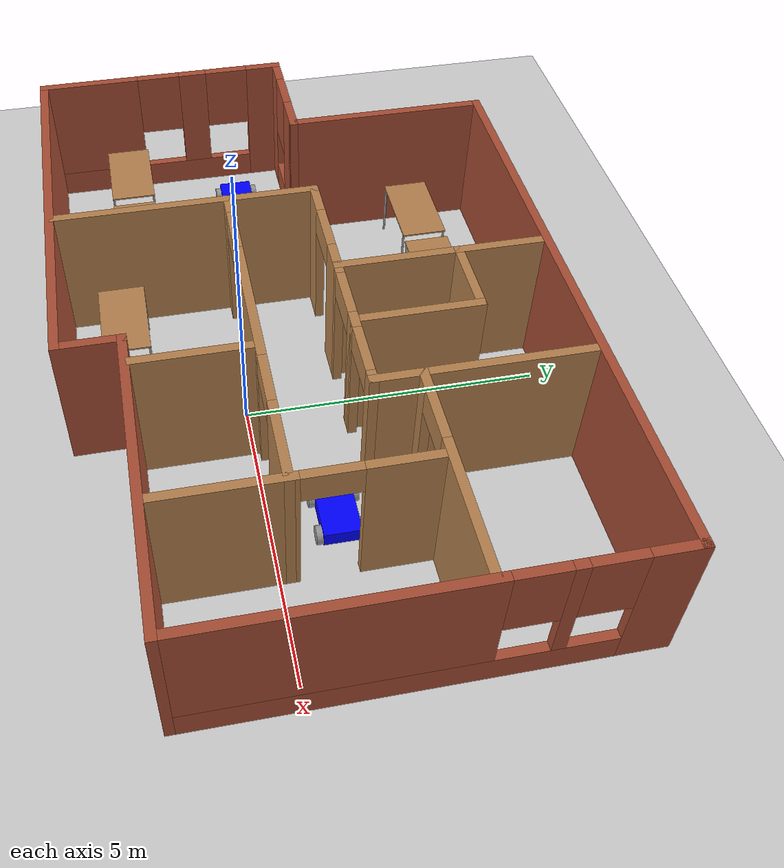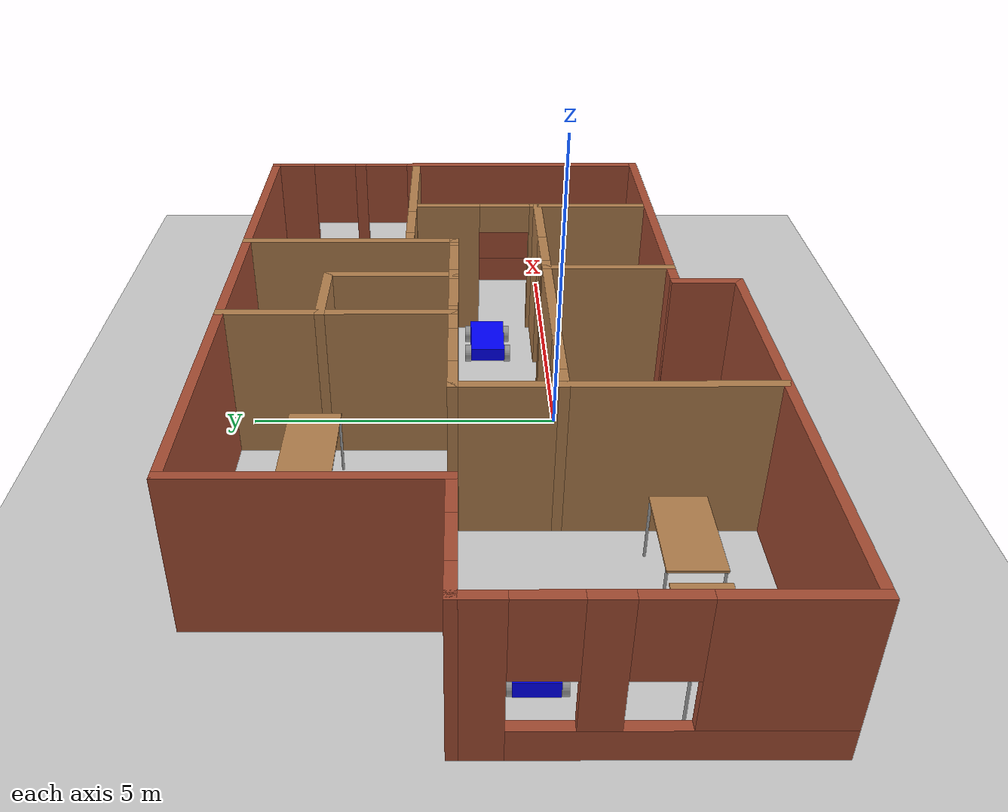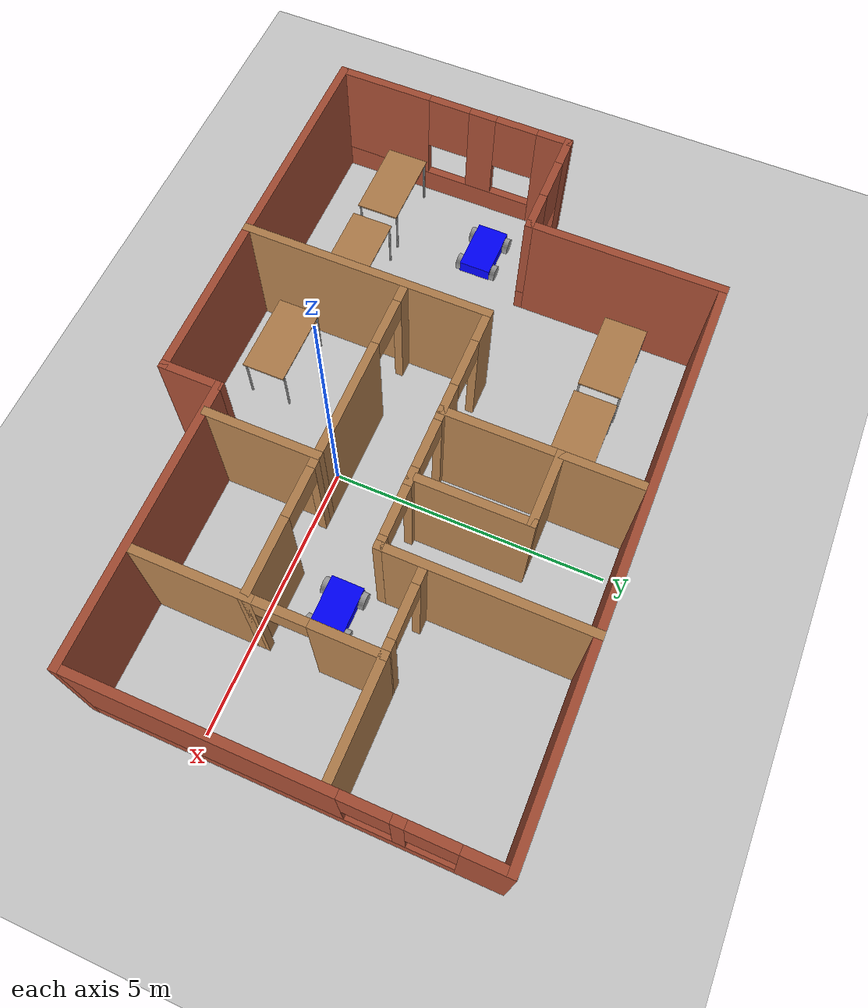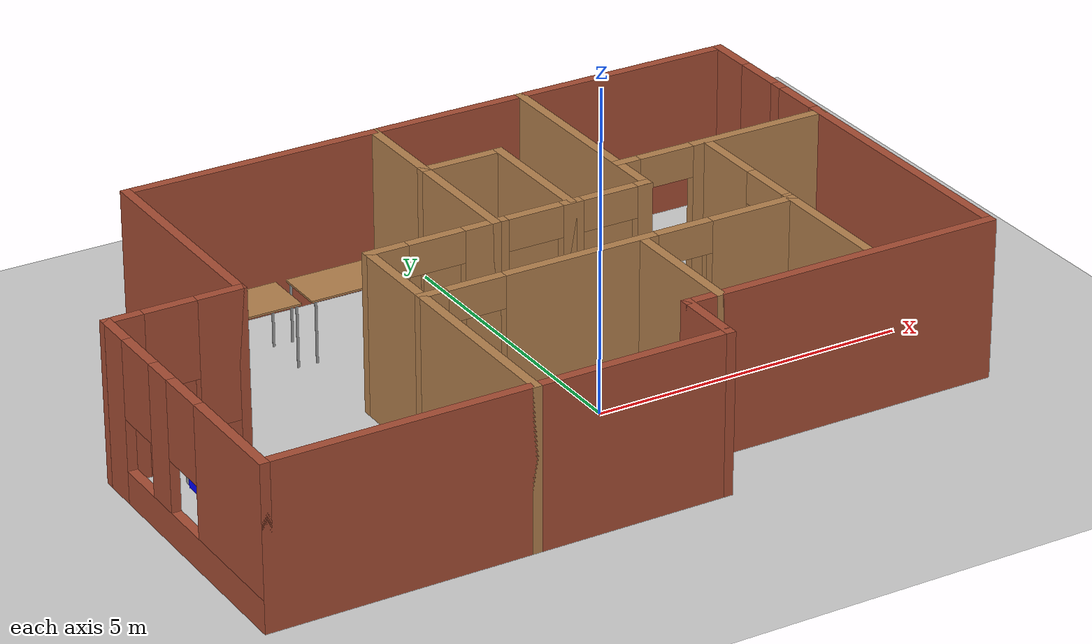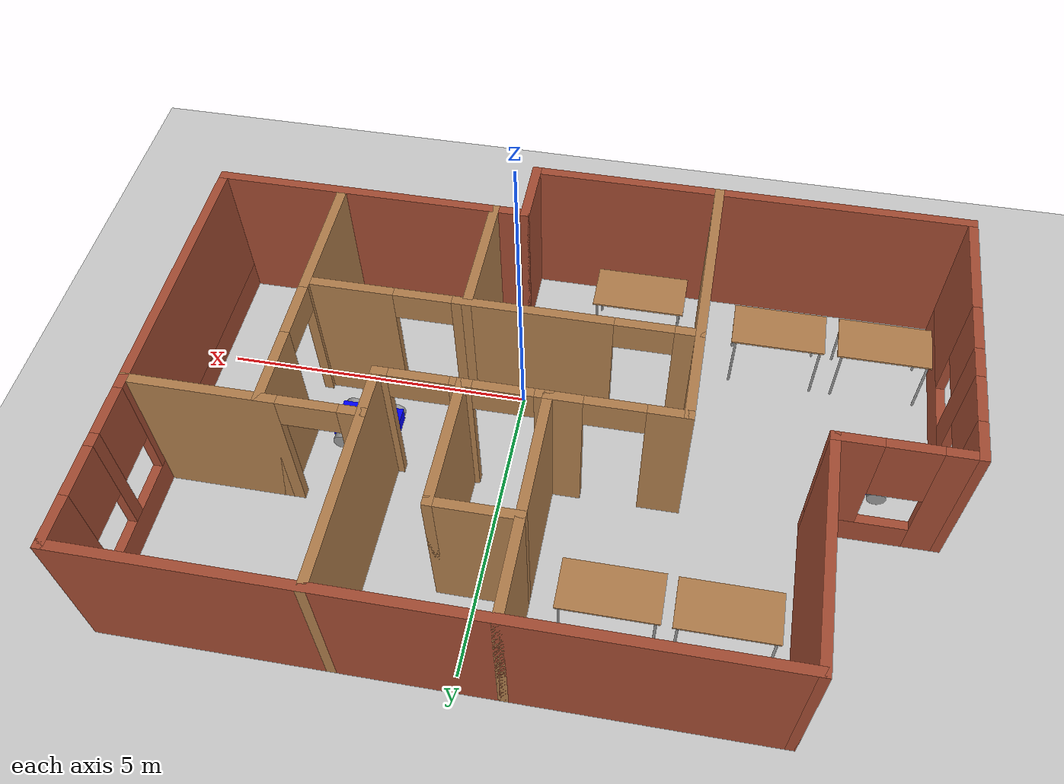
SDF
<sdf version="1.6">
 <world name="default">
  <light name="sun" type="directional">
   <pose>0 0 10 0 -0 0</pose>
   <diffuse>0.8 0.8 0.8 1</diffuse>
   <specular>0.2 0.2 0.2 1</specular>
   <attenuation>
    <range>1000</range>
    <constant>0.9</constant>
    <linear>0.01</linear>
    <quadratic>0.001</quadratic>
   </attenuation>
   <direction>-0.5 0.1 -0.9</direction>
  </light>
  <model name="ground_plane">
   <static>1</static>
   <link name="link">
    <collision name="collision">
     <geometry><plane><normal>0 0 1</normal><size>100 100</size></plane></geometry>
     <surface>
      <contact><collide_bitmask>65535</collide_bitmask></contact>
      <friction><ode><mu>100</mu><mu2>50</mu2></ode></friction>
     </surface>
    </collision>
    <visual name="visual">
     <cast_shadows>0</cast_shadows>
     <geometry><plane><normal>0 0 1</normal><size>100 100</size></plane></geometry>
     <material>
      <script><uri>file://media/materials/scripts/gazebo.material</uri><name>Gazebo/Grey</name></script>
     </material>
    </visual>
   </link>
  </model>
  <gravity>0 0 -9.8</gravity>
  <magnetic_field>6e-06 2.3e-05 -4.2e-05</magnetic_field>
  <atmosphere type="adiabatic"/>
  <physics name="default_physics" default="0" type="ode">
   <max_step_size>0.001</max_step_size>
   <real_time_factor>1</real_time_factor>
   <real_time_update_rate>1000</real_time_update_rate>
  </physics>
  <scene><ambient>0.4 0.4 0.4 1</ambient><background>0.7 0.7 0.7 1</background><shadows>1</shadows></scene>
  <spherical_coordinates>
   <surface_model>EARTH_WGS84</surface_model>
   <latitude_deg>0</latitude_deg>
   <longitude_deg>0</longitude_deg>
   <elevation>0</elevation>
   <heading_deg>0</heading_deg>
  </spherical_coordinates>
  <model name="Building">
   <pose>-0.72894 1.17252 0 0 -0 0</pose>
   <link name="Wall_53">
    <collision name="Wall_53_Collision">
     <geometry><box><size>3.65 0.15 2.5</size></box></geometry>
     <pose>0 0 1.25 0 -0 0</pose>
    </collision>
    <visual name="Wall_53_Visual">
     <pose>0 0 1.25 0 -0 0</pose>
     <geometry><box><size>3.65 0.15 2.5</size></box></geometry>
     <material>
      <script><uri>file://media/materials/scripts/gazebo.material</uri><name>Gazebo/Bricks</name></script>
      <ambient>0.0666667 0.0941176 0.498039 1</ambient>
     </material>
     <meta><layer>0</layer></meta>
    </visual>
    <pose>-3.99976 2.25 0 0 -0 1.5708</pose>
   </link>
   <link name="Wall_57">
    <pose>-5.99976 -1.75 0 0 0 -1.5708</pose>
    <visual name="Wall_57_Visual_0">
     <pose>-1.98879 0 1.25 0 -0 0</pose>
     <geometry><box><size>0.672428 0.15 2.5</size></box></geometry>
     <material>
      <script><uri>file://media/materials/scripts/gazebo.material</uri><name>Gazebo/Bricks</name></script>
      <ambient>0.0666667 0.0941176 0.498039 1</ambient>
     </material>
     <meta><layer>0</layer></meta>
    </visual>
    <collision name="Wall_57_Collision_0">
     <geometry><box><size>0.672428 0.15 2.5</size></box></geometry>
     <pose>-1.98879 0 1.25 0 -0 0</pose>
    </collision>
    <visual name="Wall_57_Visual_1">
     <pose>0.336214 0 0.25 0 -0 0</pose>
     <geometry><box><size>3.97757 0.15 0.5</size></box></geometry>
     <material>
      <script><uri>file://media/materials/scripts/gazebo.material</uri><name>Gazebo/Bricks</name></script>
      <ambient>0.0666667 0.0941176 0.498039 1</ambient>
     </material>
     <meta><layer>0</layer></meta>
    </visual>
    <collision name="Wall_57_Collision_1">
     <geometry><box><size>3.97757 0.15 0.5</size></box></geometry>
     <pose>0.336214 0 0.25 0 -0 0</pose>
    </collision>
    <visual name="Wall_57_Visual_2">
     <pose>-0.591148 0 1.5 0 -0 0</pose>
     <geometry><box><size>0.522849 0.15 2</size></box></geometry>
     <material>
      <script><uri>file://media/materials/scripts/gazebo.material</uri><name>Gazebo/Bricks</name></script>
      <ambient>0.0666667 0.0941176 0.498039 1</ambient>
     </material>
     <meta><layer>0</layer></meta>
    </visual>
    <collision name="Wall_57_Collision_2">
     <geometry><box><size>0.522849 0.15 2</size></box></geometry>
     <pose>-0.591148 0 1.5 0 -0 0</pose>
    </collision>
    <visual name="Wall_57_Visual_3">
     <pose>1.39764 0 1.5 0 -0 0</pose>
     <geometry><box><size>1.85472 0.15 2</size></box></geometry>
     <material>
      <script><uri>file://media/materials/scripts/gazebo.material</uri><name>Gazebo/Bricks</name></script>
      <ambient>0.0666667 0.0941176 0.498039 1</ambient>
     </material>
     <meta><layer>0</layer></meta>
    </visual>
    <collision name="Wall_57_Collision_3">
     <geometry><box><size>1.85472 0.15 2</size></box></geometry>
     <pose>1.39764 0 1.5 0 -0 0</pose>
    </collision>
    <visual name="Wall_57_Visual_4">
     <pose>-1.25257 0 1.9 0 -0 0</pose>
     <geometry><box><size>0.8 0.15 1.2</size></box></geometry>
     <material>
      <script><uri>file://media/materials/scripts/gazebo.material</uri><name>Gazebo/Bricks</name></script>
      <ambient>0.0666667 0.0941176 0.498039 1</ambient>
     </material>
     <meta><layer>0</layer></meta>
    </visual>
    <collision name="Wall_57_Collision_4">
     <geometry><box><size>0.8 0.15 1.2</size></box></geometry>
     <pose>-1.25257 0 1.9 0 -0 0</pose>
    </collision>
    <visual name="Wall_57_Visual_5">
     <pose>0.070277 0 1.9 0 -0 0</pose>
     <geometry><box><size>0.8 0.15 1.2</size></box></geometry>
     <material>
      <script><uri>file://media/materials/scripts/gazebo.material</uri><name>Gazebo/Bricks</name></script>
      <ambient>0.0666667 0.0941176 0.498039 1</ambient>
     </material>
     <meta><layer>0</layer></meta>
    </visual>
    <collision name="Wall_57_Collision_5">
     <geometry><box><size>0.8 0.15 1.2</size></box></geometry>
     <pose>0.070277 0 1.9 0 -0 0</pose>
    </collision>
   </link>
   <link name="Wall_59">
    <collision name="Wall_59_Collision">
     <geometry><box><size>7.15 0.15 2.5</size></box></geometry>
     <pose>0 0 1.25 0 -0 0</pose>
    </collision>
    <visual name="Wall_59_Visual">
     <pose>0 0 1.25 0 -0 0</pose>
     <geometry><box><size>7.15 0.15 2.5</size></box></geometry>
     <material>
      <script><uri>file://media/materials/scripts/gazebo.material</uri><name>Gazebo/Bricks</name></script>
      <ambient>0.0666667 0.0941176 0.498039 1</ambient>
     </material>
     <meta><layer>0</layer></meta>
    </visual>
    <pose>-2.49976 -4 0 0 -0 0</pose>
   </link>
   <link name="Wall_61">
    <collision name="Wall_61_Collision">
     <geometry><box><size>1.15 0.15 2.5</size></box></geometry>
     <pose>0 0 1.25 0 -0 0</pose>
    </collision>
    <visual name="Wall_61_Visual">
     <pose>0 0 1.25 0 -0 0</pose>
     <geometry><box><size>1.15 0.15 2.5</size></box></geometry>
     <material>
      <script><uri>file://media/materials/scripts/gazebo.material</uri><name>Gazebo/Bricks</name></script>
      <ambient>0.0666667 0.0941176 0.498039 1</ambient>
     </material>
     <meta><layer>0</layer></meta>
    </visual>
    <pose>1.00024 -3.5 0 0 -0 1.5708</pose>
   </link>
   <link name="Wall_63">
    <collision name="Wall_63_Collision">
     <geometry><box><size>5.15 0.15 2.5</size></box></geometry>
     <pose>0 0 1.25 0 -0 0</pose>
    </collision>
    <visual name="Wall_63_Visual">
     <pose>0 0 1.25 0 -0 0</pose>
     <geometry><box><size>5.15 0.15 2.5</size></box></geometry>
     <material>
      <script><uri>file://media/materials/scripts/gazebo.material</uri><name>Gazebo/Bricks</name></script>
      <ambient>0.0666667 0.0941176 0.498039 1</ambient>
     </material>
     <meta><layer>0</layer></meta>
    </visual>
    <pose>3.50024 -3 0 0 -0 0</pose>
   </link>
   <link name="Wall_65">
    <collision name="Wall_65_Collision">
     <geometry><box><size>10.15 0.15 2.5</size></box></geometry>
     <pose>0 0 1.25 0 -0 0</pose>
    </collision>
    <visual name="Wall_65_Visual">
     <pose>0 0 1.25 0 -0 0</pose>
     <geometry><box><size>10.15 0.15 2.5</size></box></geometry>
     <material>
      <script><uri>file://media/materials/scripts/gazebo.material</uri><name>Gazebo/Bricks</name></script>
      <ambient>0.0666667 0.0941176 0.498039 1</ambient>
     </material>
     <meta><layer>0</layer></meta>
    </visual>
    <pose>1.00024 4 0 0 -0 0</pose>
   </link>
   <link name="Wall_68">
    <pose>6.00024 0.575 0 0 0 -1.5708</pose>
    <visual name="Wall_68_Visual_0">
     <pose>-3.09042 0 1.25 0 -0 0</pose>
     <geometry><box><size>0.819158 0.15 2.5</size></box></geometry>
     <material>
      <script><uri>file://media/materials/scripts/gazebo.material</uri><name>Gazebo/Bricks</name></script>
      <ambient>0 0 0.498039 1</ambient>
     </material>
     <meta><layer>0</layer></meta>
    </visual>
    <collision name="Wall_68_Collision_0">
     <geometry><box><size>0.819158 0.15 2.5</size></box></geometry>
     <pose>-3.09042 0 1.25 0 -0 0</pose>
    </collision>
    <visual name="Wall_68_Visual_1">
     <pose>0.409579 0 0.25 0 -0 0</pose>
     <geometry><box><size>6.18084 0.15 0.5</size></box></geometry>
     <material>
      <script><uri>file://media/materials/scripts/gazebo.material</uri><name>Gazebo/Bricks</name></script>
      <ambient>0 0 0.498039 1</ambient>
     </material>
     <meta><layer>0</layer></meta>
    </visual>
    <collision name="Wall_68_Collision_1">
     <geometry><box><size>6.18084 0.15 0.5</size></box></geometry>
     <pose>0.409579 0 0.25 0 -0 0</pose>
    </collision>
    <visual name="Wall_68_Visual_2">
     <pose>-1.77324 0 1.5 0 -0 0</pose>
     <geometry><box><size>0.21521 0.15 2</size></box></geometry>
     <material>
      <script><uri>file://media/materials/scripts/gazebo.material</uri><name>Gazebo/Bricks</name></script>
      <ambient>0 0 0.498039 1</ambient>
     </material>
     <meta><layer>0</layer></meta>
    </visual>
    <collision name="Wall_68_Collision_2">
     <geometry><box><size>0.21521 0.15 2</size></box></geometry>
     <pose>-1.77324 0 1.5 0 -0 0</pose>
    </collision>
    <visual name="Wall_68_Visual_3">
     <pose>1.31718 0 1.5 0 -0 0</pose>
     <geometry><box><size>4.36563 0.15 2</size></box></geometry>
     <material>
      <script><uri>file://media/materials/scripts/gazebo.material</uri><name>Gazebo/Bricks</name></script>
      <ambient>0 0 0.498039 1</ambient>
     </material>
     <meta><layer>0</layer></meta>
    </visual>
    <collision name="Wall_68_Collision_3">
     <geometry><box><size>4.36563 0.15 2</size></box></geometry>
     <pose>1.31718 0 1.5 0 -0 0</pose>
    </collision>
    <visual name="Wall_68_Visual_4">
     <pose>-2.28084 0 1.9 0 -0 0</pose>
     <geometry><box><size>0.8 0.15 1.2</size></box></geometry>
     <material>
      <script><uri>file://media/materials/scripts/gazebo.material</uri><name>Gazebo/Bricks</name></script>
      <ambient>0 0 0.498039 1</ambient>
     </material>
     <meta><layer>0</layer></meta>
    </visual>
    <collision name="Wall_68_Collision_4">
     <geometry><box><size>0.8 0.15 1.2</size></box></geometry>
     <pose>-2.28084 0 1.9 0 -0 0</pose>
    </collision>
    <visual name="Wall_68_Visual_5">
     <pose>-1.26563 0 1.9 0 -0 0</pose>
     <geometry><box><size>0.8 0.15 1.2</size></box></geometry>
     <material>
      <script><uri>file://media/materials/scripts/gazebo.material</uri><name>Gazebo/Bricks</name></script>
      <ambient>0 0 0.498039 1</ambient>
     </material>
     <meta><layer>0</layer></meta>
    </visual>
    <collision name="Wall_68_Collision_5">
     <geometry><box><size>0.8 0.15 1.2</size></box></geometry>
     <pose>-1.26563 0 1.9 0 -0 0</pose>
    </collision>
   </link>
   <link name="Wall_70">
    <collision name="Wall_70_Collision">
     <geometry><box><size>3.65 0.15 2.5</size></box></geometry>
     <pose>0 0 1.25 0 -0 0</pose>
    </collision>
    <visual name="Wall_70_Visual">
     <pose>0 0 1.25 0 -0 0</pose>
     <geometry><box><size>3.65 0.15 2.5</size></box></geometry>
     <material>
      <script><uri>file://media/materials/scripts/gazebo.material</uri><name>Gazebo/Wood</name></script>
      <ambient>0 0 0.498039 1</ambient>
     </material>
     <meta><layer>0</layer></meta>
    </visual>
    <pose>0.000236 2.25 0 0 0 -1.5708</pose>
   </link>
   <link name="Wall_72">
    <pose>-0.999764 0.5 0 0 -0 3.14159</pose>
    <visual name="Wall_72_Visual_0">
     <pose>-0.784599 0 1.25 0 -0 0</pose>
     <geometry><box><size>0.580802 0.15 2.5</size></box></geometry>
     <material>
      <script><uri>file://media/materials/scripts/gazebo.material</uri><name>Gazebo/Wood</name></script>
      <ambient>0 0 0.498039 1</ambient>
     </material>
     <meta><layer>0</layer></meta>
    </visual>
    <collision name="Wall_72_Collision_0">
     <geometry><box><size>0.580802 0.15 2.5</size></box></geometry>
     <pose>-0.784599 0 1.25 0 -0 0</pose>
    </collision>
    <visual name="Wall_72_Visual_1">
     <pose>0.740401 0 1.25 0 -0 0</pose>
     <geometry><box><size>0.669198 0.15 2.5</size></box></geometry>
     <material>
      <script><uri>file://media/materials/scripts/gazebo.material</uri><name>Gazebo/Wood</name></script>
      <ambient>0 0 0.498039 1</ambient>
     </material>
     <meta><layer>0</layer></meta>
    </visual>
    <collision name="Wall_72_Collision_1">
     <geometry><box><size>0.669198 0.15 2.5</size></box></geometry>
     <pose>0.740401 0 1.25 0 -0 0</pose>
    </collision>
    <visual name="Wall_72_Visual_2">
     <pose>-0.044198 0 2.25 0 -0 0</pose>
     <geometry><box><size>0.9 0.15 0.5</size></box></geometry>
     <material>
      <script><uri>file://media/materials/scripts/gazebo.material</uri><name>Gazebo/Wood</name></script>
      <ambient>0 0 0.498039 1</ambient>
     </material>
     <meta><layer>0</layer></meta>
    </visual>
    <collision name="Wall_72_Collision_2">
     <geometry><box><size>0.9 0.15 0.5</size></box></geometry>
     <pose>-0.044198 0 2.25 0 -0 0</pose>
    </collision>
   </link>
   <link name="Wall_76">
    <pose>-4.99976 0.5 0 0 -0 0</pose>
    <visual name="Wall_76_Visual_0">
     <pose>-0.776822 0 1.25 0 -0 0</pose>
     <geometry><box><size>0.597303 0.15 2.5</size></box></geometry>
     <material>
      <script><uri>file://media/materials/scripts/gazebo.material</uri><name>Gazebo/Bricks</name></script>
      <ambient>0.0666667 0.0941176 0.498039 1</ambient>
     </material>
     <meta><layer>0</layer></meta>
    </visual>
    <collision name="Wall_76_Collision_0">
     <geometry><box><size>0.597303 0.15 2.5</size></box></geometry>
     <pose>-0.776822 0 1.25 0 -0 0</pose>
    </collision>
    <visual name="Wall_76_Visual_1">
     <pose>0.298651 0 0.25 0 -0 0</pose>
     <geometry><box><size>1.55364 0.15 0.5</size></box></geometry>
     <material>
      <script><uri>file://media/materials/scripts/gazebo.material</uri><name>Gazebo/Bricks</name></script>
      <ambient>0.0666667 0.0941176 0.498039 1</ambient>
     </material>
     <meta><layer>0</layer></meta>
    </visual>
    <collision name="Wall_76_Collision_1">
     <geometry><box><size>1.55364 0.15 0.5</size></box></geometry>
     <pose>0.298651 0 0.25 0 -0 0</pose>
    </collision>
    <visual name="Wall_76_Visual_2">
     <pose>0.698651 0 1.5 0 -0 0</pose>
     <geometry><box><size>0.753643 0.15 2</size></box></geometry>
     <material>
      <script><uri>file://media/materials/scripts/gazebo.material</uri><name>Gazebo/Bricks</name></script>
      <ambient>0.0666667 0.0941176 0.498039 1</ambient>
     </material>
     <meta><layer>0</layer></meta>
    </visual>
    <collision name="Wall_76_Collision_2">
     <geometry><box><size>0.753643 0.15 2</size></box></geometry>
     <pose>0.698651 0 1.5 0 -0 0</pose>
    </collision>
    <visual name="Wall_76_Visual_3">
     <pose>-0.07817 0 1.9 0 -0 0</pose>
     <geometry><box><size>0.8 0.15 1.2</size></box></geometry>
     <material>
      <script><uri>file://media/materials/scripts/gazebo.material</uri><name>Gazebo/Bricks</name></script>
      <ambient>0.0666667 0.0941176 0.498039 1</ambient>
     </material>
     <meta><layer>0</layer></meta>
    </visual>
    <collision name="Wall_76_Collision_3">
     <geometry><box><size>0.8 0.15 1.2</size></box></geometry>
     <pose>-0.07817 0 1.9 0 -0 0</pose>
    </collision>
   </link>
   <link name="Wall_78">
    <collision name="Wall_78_Collision">
     <geometry><box><size>4.65 0.15 2.5</size></box></geometry>
     <pose>0 0 1.25 0 -0 0</pose>
    </collision>
    <visual name="Wall_78_Visual">
     <pose>0 0 1.25 0 -0 0</pose>
     <geometry><box><size>4.65 0.15 2.5</size></box></geometry>
     <material>
      <script><uri>file://media/materials/scripts/gazebo.material</uri><name>Gazebo/Wood</name></script>
      <ambient>0 0 0.498039 1</ambient>
     </material>
     <meta><layer>0</layer></meta>
    </visual>
    <pose>-1.99976 -1.75 0 0 0 -1.5708</pose>
   </link>
   <link name="Wall_80">
    <collision name="Wall_80_Collision">
     <geometry><box><size>3.65 0.15 2.5</size></box></geometry>
     <pose>0 0 1.25 0 -0 0</pose>
    </collision>
    <visual name="Wall_80_Visual">
     <pose>0 0 1.25 0 -0 0</pose>
     <geometry><box><size>3.65 0.15 2.5</size></box></geometry>
     <material>
      <script><uri>file://media/materials/scripts/gazebo.material</uri><name>Gazebo/Wood</name></script>
      <ambient>0 0 0.498039 1</ambient>
     </material>
     <meta><layer>0</layer></meta>
    </visual>
    <pose>2.50024 2.25 0 0 0 -1.5708</pose>
   </link>
   <link name="Wall_83">
    <pose>1.25024 0.5 0 0 -0 3.14159</pose>
    <visual name="Wall_83_Visual_0">
     <pose>-1.19974 0 1.25 0 -0 0</pose>
     <geometry><box><size>0.25052 0.15 2.5</size></box></geometry>
     <material>
      <script><uri>file://media/materials/scripts/gazebo.material</uri><name>Gazebo/Wood</name></script>
      <ambient>0 0 0.498039 1</ambient>
     </material>
     <meta><layer>0</layer></meta>
    </visual>
    <collision name="Wall_83_Collision_0">
     <geometry><box><size>0.25052 0.15 2.5</size></box></geometry>
     <pose>-1.19974 0 1.25 0 -0 0</pose>
    </collision>
    <visual name="Wall_83_Visual_1">
     <pose>-0.009201 0 1.25 0 -0 0</pose>
     <geometry><box><size>0.330557 0.15 2.5</size></box></geometry>
     <material>
      <script><uri>file://media/materials/scripts/gazebo.material</uri><name>Gazebo/Wood</name></script>
      <ambient>0 0 0.498039 1</ambient>
     </material>
     <meta><layer>0</layer></meta>
    </visual>
    <collision name="Wall_83_Collision_1">
     <geometry><box><size>0.330557 0.15 2.5</size></box></geometry>
     <pose>-0.009201 0 1.25 0 -0 0</pose>
    </collision>
    <visual name="Wall_83_Visual_2">
     <pose>1.19054 0 1.25 0 -0 0</pose>
     <geometry><box><size>0.268922 0.15 2.5</size></box></geometry>
     <material>
      <script><uri>file://media/materials/scripts/gazebo.material</uri><name>Gazebo/Wood</name></script>
      <ambient>0 0 0.498039 1</ambient>
     </material>
     <meta><layer>0</layer></meta>
    </visual>
    <collision name="Wall_83_Collision_2">
     <geometry><box><size>0.268922 0.15 2.5</size></box></geometry>
     <pose>1.19054 0 1.25 0 -0 0</pose>
    </collision>
    <visual name="Wall_83_Visual_3">
     <pose>-0.62448 0 2.25 0 -0 0</pose>
     <geometry><box><size>0.9 0.15 0.5</size></box></geometry>
     <material>
      <script><uri>file://media/materials/scripts/gazebo.material</uri><name>Gazebo/Wood</name></script>
      <ambient>0 0 0.498039 1</ambient>
     </material>
     <meta><layer>0</layer></meta>
    </visual>
    <collision name="Wall_83_Collision_3">
     <geometry><box><size>0.9 0.15 0.5</size></box></geometry>
     <pose>-0.62448 0 2.25 0 -0 0</pose>
    </collision>
    <visual name="Wall_83_Visual_4">
     <pose>0.606078 0 2.25 0 -0 0</pose>
     <geometry><box><size>0.9 0.15 0.5</size></box></geometry>
     <material>
      <script><uri>file://media/materials/scripts/gazebo.material</uri><name>Gazebo/Wood</name></script>
      <ambient>0 0 0.498039 1</ambient>
     </material>
     <meta><layer>0</layer></meta>
    </visual>
    <collision name="Wall_83_Collision_4">
     <geometry><box><size>0.9 0.15 0.5</size></box></geometry>
     <pose>0.606078 0 2.25 0 -0 0</pose>
    </collision>
   </link>
   <link name="Wall_87">
    <pose>4.25024 1.25 0 0 -0 0</pose>
    <visual name="Wall_87_Visual_0">
     <pose>-1.61769 0 1.25 0 -0 0</pose>
     <geometry><box><size>0.414621 0.15 2.5</size></box></geometry>
     <material>
      <script><uri>file://media/materials/scripts/gazebo.material</uri><name>Gazebo/Wood</name></script>
      <ambient>0 0 0.498039 1</ambient>
     </material>
     <meta><layer>0</layer></meta>
    </visual>
    <collision name="Wall_87_Collision_0">
     <geometry><box><size>0.414621 0.15 2.5</size></box></geometry>
     <pose>-1.61769 0 1.25 0 -0 0</pose>
    </collision>
    <visual name="Wall_87_Visual_1">
     <pose>0.65731 0 1.25 0 -0 0</pose>
     <geometry><box><size>2.33538 0.15 2.5</size></box></geometry>
     <material>
      <script><uri>file://media/materials/scripts/gazebo.material</uri><name>Gazebo/Wood</name></script>
      <ambient>0 0 0.498039 1</ambient>
     </material>
     <meta><layer>0</layer></meta>
    </visual>
    <collision name="Wall_87_Collision_1">
     <geometry><box><size>2.33538 0.15 2.5</size></box></geometry>
     <pose>0.65731 0 1.25 0 -0 0</pose>
    </collision>
    <visual name="Wall_87_Visual_2">
     <pose>-0.960379 0 2.25 0 -0 0</pose>
     <geometry><box><size>0.9 0.15 0.5</size></box></geometry>
     <material>
      <script><uri>file://media/materials/scripts/gazebo.material</uri><name>Gazebo/Wood</name></script>
      <ambient>0 0 0.498039 1</ambient>
     </material>
     <meta><layer>0</layer></meta>
    </visual>
    <collision name="Wall_87_Collision_2">
     <geometry><box><size>0.9 0.15 0.5</size></box></geometry>
     <pose>-0.960379 0 2.25 0 -0 0</pose>
    </collision>
   </link>
   <link name="Wall_89">
    <pose>4.00024 -0.8 0 0 0 -1.5708</pose>
    <visual name="Wall_89_Visual_0">
     <pose>-1.48493 0 1.25 0 -0 0</pose>
     <geometry><box><size>1.28014 0.15 2.5</size></box></geometry>
     <material>
      <script><uri>file://media/materials/scripts/gazebo.material</uri><name>Gazebo/Wood</name></script>
      <ambient>0 0 0.498039 1</ambient>
     </material>
     <meta><layer>0</layer></meta>
    </visual>
    <collision name="Wall_89_Collision_0">
     <geometry><box><size>1.28014 0.15 2.5</size></box></geometry>
     <pose>-1.48493 0 1.25 0 -0 0</pose>
    </collision>
    <visual name="Wall_89_Visual_1">
     <pose>1.09007 0 1.25 0 -0 0</pose>
     <geometry><box><size>2.06986 0.15 2.5</size></box></geometry>
     <material>
      <script><uri>file://media/materials/scripts/gazebo.material</uri><name>Gazebo/Wood</name></script>
      <ambient>0 0 0.498039 1</ambient>
     </material>
     <meta><layer>0</layer></meta>
    </visual>
    <collision name="Wall_89_Collision_1">
     <geometry><box><size>2.06986 0.15 2.5</size></box></geometry>
     <pose>1.09007 0 1.25 0 -0 0</pose>
    </collision>
    <visual name="Wall_89_Visual_2">
     <pose>-0.394864 0 2.25 0 -0 0</pose>
     <geometry><box><size>0.9 0.15 0.5</size></box></geometry>
     <material>
      <script><uri>file://media/materials/scripts/gazebo.material</uri><name>Gazebo/Wood</name></script>
      <ambient>0 0 0.498039 1</ambient>
     </material>
     <meta><layer>0</layer></meta>
    </visual>
    <collision name="Wall_89_Collision_2">
     <geometry><box><size>0.9 0.15 0.5</size></box></geometry>
     <pose>-0.394864 0 2.25 0 -0 0</pose>
    </collision>
   </link>
   <link name="Wall_92">
    <pose>1.00024 -1 0 0 -0 3.14159</pose>
    <visual name="Wall_92_Visual_0">
     <pose>-2.35356 0 1.25 0 -0 0</pose>
     <geometry><box><size>1.44288 0.15 2.5</size></box></geometry>
     <material>
      <script><uri>file://media/materials/scripts/gazebo.material</uri><name>Gazebo/Wood</name></script>
      <ambient>0 0 0.498039 1</ambient>
     </material>
     <meta><layer>0</layer></meta>
    </visual>
    <collision name="Wall_92_Collision_0">
     <geometry><box><size>1.44288 0.15 2.5</size></box></geometry>
     <pose>-2.35356 0 1.25 0 -0 0</pose>
    </collision>
    <visual name="Wall_92_Visual_1">
     <pose>0.494515 0 1.25 0 -0 0</pose>
     <geometry><box><size>2.45327 0.15 2.5</size></box></geometry>
     <material>
      <script><uri>file://media/materials/scripts/gazebo.material</uri><name>Gazebo/Wood</name></script>
      <ambient>0 0 0.498039 1</ambient>
     </material>
     <meta><layer>0</layer></meta>
    </visual>
    <collision name="Wall_92_Collision_1">
     <geometry><box><size>2.45327 0.15 2.5</size></box></geometry>
     <pose>0.494515 0 1.25 0 -0 0</pose>
    </collision>
    <visual name="Wall_92_Visual_2">
     <pose>2.84808 0 1.25 0 -0 0</pose>
     <geometry><box><size>0.45385 0.15 2.5</size></box></geometry>
     <material>
      <script><uri>file://media/materials/scripts/gazebo.material</uri><name>Gazebo/Wood</name></script>
      <ambient>0 0 0.498039 1</ambient>
     </material>
     <meta><layer>0</layer></meta>
    </visual>
    <collision name="Wall_92_Collision_2">
     <geometry><box><size>0.45385 0.15 2.5</size></box></geometry>
     <pose>2.84808 0 1.25 0 -0 0</pose>
    </collision>
    <visual name="Wall_92_Visual_3">
     <pose>-1.18212 0 2.25 0 -0 0</pose>
     <geometry><box><size>0.9 0.15 0.5</size></box></geometry>
     <material>
      <script><uri>file://media/materials/scripts/gazebo.material</uri><name>Gazebo/Wood</name></script>
      <ambient>0 0 0.498039 1</ambient>
     </material>
     <meta><layer>0</layer></meta>
    </visual>
    <collision name="Wall_92_Collision_3">
     <geometry><box><size>0.9 0.15 0.5</size></box></geometry>
     <pose>-1.18212 0 2.25 0 -0 0</pose>
    </collision>
    <visual name="Wall_92_Visual_4">
     <pose>2.17115 0 2.25 0 -0 0</pose>
     <geometry><box><size>0.9 0.15 0.5</size></box></geometry>
     <material>
      <script><uri>file://media/materials/scripts/gazebo.material</uri><name>Gazebo/Wood</name></script>
      <ambient>0 0 0.498039 1</ambient>
     </material>
     <meta><layer>0</layer></meta>
    </visual>
    <collision name="Wall_92_Collision_4">
     <geometry><box><size>0.9 0.15 0.5</size></box></geometry>
     <pose>2.17115 0 2.25 0 -0 0</pose>
    </collision>
   </link>
   <link name="Wall_94">
    <collision name="Wall_94_Collision">
     <geometry><box><size>2.15 0.15 2.5</size></box></geometry>
     <pose>0 0 1.25 0 -0 0</pose>
    </collision>
    <visual name="Wall_94_Visual">
     <pose>0 0 1.25 0 -0 0</pose>
     <geometry><box><size>2.15 0.15 2.5</size></box></geometry>
     <material>
      <script><uri>file://media/materials/scripts/gazebo.material</uri><name>Gazebo/Wood</name></script>
      <ambient>0 0 0.498039 1</ambient>
     </material>
     <meta><layer>0</layer></meta>
    </visual>
    <pose>1.50024 -2 0 0 0 -1.5708</pose>
   </link>
   <link name="Wall_96">
    <collision name="Wall_96_Collision">
     <geometry><box><size>1.4 0.15 2.5</size></box></geometry>
     <pose>0 0 1.25 0 -0 0</pose>
    </collision>
    <visual name="Wall_96_Visual">
     <pose>0 0 1.25 0 -0 0</pose>
     <geometry><box><size>1.4 0.15 2.5</size></box></geometry>
     <material>
      <script><uri>file://media/materials/scripts/gazebo.material</uri><name>Gazebo/Wood</name></script>
      <ambient>0 0 0.498039 1</ambient>
     </material>
     <meta><layer>0</layer></meta>
    </visual>
    <pose>0.625236 2.5 0 0 -0 0</pose>
   </link>
   <link name="Wall_97">
    <collision name="Wall_97_Collision">
     <geometry><box><size>2.15 0.15 2.5</size></box></geometry>
     <pose>0 0 1.25 0 -0 0</pose>
    </collision>
    <visual name="Wall_97_Visual">
     <pose>0 0 1.25 0 -0 0</pose>
     <geometry><box><size>2.15 0.15 2.5</size></box></geometry>
     <material>
      <script><uri>file://media/materials/scripts/gazebo.material</uri><name>Gazebo/Wood</name></script>
      <ambient>0 0 0.498039 1</ambient>
     </material>
     <meta><layer>0</layer></meta>
    </visual>
    <pose>1.25024 1.5 0 0 0 -1.5708</pose>
   </link>
   <static>1</static>
  </model>
  <light name="user_point_light_1" type="point">
   <pose>-5.02493 -0.52495 1 0 -0 0</pose>
   <diffuse>0.5 0.5 0.5 1</diffuse>
   <specular>0.1 0.1 0.1 1</specular>
   <attenuation>
    <range>20</range>
    <constant>0.5</constant>
    <linear>0.01</linear>
    <quadratic>0.001</quadratic>
   </attenuation>
   <cast_shadows>0</cast_shadows>
   <direction>0 0 -1</direction>
  </light>
  <model name="table">
   <static>1</static>
   <link name="link">
    <collision name="surface">
     <pose>0 0 1 0 -0 0</pose>
     <geometry><box><size>1.5 0.8 0.03</size></box></geometry>
     <surface><friction><ode><mu>0.6</mu><mu2>0.6</mu2></ode></friction></surface>
    </collision>
    <visual name="visual1">
     <pose>0 0 1 0 -0 0</pose>
     <geometry><box><size>1.5 0.8 0.03</size></box></geometry>
     <material>
      <script><uri>file://media/materials/scripts/gazebo.material</uri><name>Gazebo/Wood</name></script>
     </material>
    </visual>
    <collision name="front_left_leg">
     <pose>0.68 0.38 0.5 0 -0 0</pose>
     <geometry><cylinder><radius>0.02</radius><length>1</length></cylinder></geometry>
    </collision>
    <visual name="front_left_leg">
     <pose>0.68 0.38 0.5 0 -0 0</pose>
     <geometry><cylinder><radius>0.02</radius><length>1</length></cylinder></geometry>
     <material>
      <script><uri>file://media/materials/scripts/gazebo.material</uri><name>Gazebo/Grey</name></script>
     </material>
    </visual>
    <collision name="front_right_leg">
     <pose>0.68 -0.38 0.5 0 -0 0</pose>
     <geometry><cylinder><radius>0.02</radius><length>1</length></cylinder></geometry>
    </collision>
    <visual name="front_right_leg">
     <pose>0.68 -0.38 0.5 0 -0 0</pose>
     <geometry><cylinder><radius>0.02</radius><length>1</length></cylinder></geometry>
     <material>
      <script><uri>file://media/materials/scripts/gazebo.material</uri><name>Gazebo/Grey</name></script>
     </material>
    </visual>
    <collision name="back_right_leg">
     <pose>-0.68 -0.38 0.5 0 -0 0</pose>
     <geometry><cylinder><radius>0.02</radius><length>1</length></cylinder></geometry>
    </collision>
    <visual name="back_right_leg">
     <pose>-0.68 -0.38 0.5 0 -0 0</pose>
     <geometry><cylinder><radius>0.02</radius><length>1</length></cylinder></geometry>
     <material>
      <script><uri>file://media/materials/scripts/gazebo.material</uri><name>Gazebo/Grey</name></script>
     </material>
    </visual>
    <collision name="back_left_leg">
     <pose>-0.68 0.38 0.5 0 -0 0</pose>
     <geometry><cylinder><radius>0.02</radius><length>1</length></cylinder></geometry>
    </collision>
    <visual name="back_left_leg">
     <pose>-0.68 0.38 0.5 0 -0 0</pose>
     <geometry><cylinder><radius>0.02</radius><length>1</length></cylinder></geometry>
     <material>
      <script><uri>file://media/materials/scripts/gazebo.material</uri><name>Gazebo/Grey</name></script>
     </material>
    </visual>
   </link>
   <pose>-1.99795 3.78498 0 0 -0 0</pose>
  </model>
  <model name="table_0">
   <static>1</static>
   <link name="link">
    <collision name="surface">
     <pose>0 0 1 0 -0 0</pose>
     <geometry><box><size>1.5 0.8 0.03</size></box></geometry>
     <surface><friction><ode><mu>0.6</mu><mu2>0.6</mu2></ode></friction></surface>
    </collision>
    <visual name="visual1">
     <pose>0 0 1 0 -0 0</pose>
     <geometry><box><size>1.5 0.8 0.03</size></box></geometry>
     <material>
      <script><uri>file://media/materials/scripts/gazebo.material</uri><name>Gazebo/Wood</name></script>
     </material>
    </visual>
    <collision name="front_left_leg">
     <pose>0.68 0.38 0.5 0 -0 0</pose>
     <geometry><cylinder><radius>0.02</radius><length>1</length></cylinder></geometry>
    </collision>
    <visual name="front_left_leg">
     <pose>0.68 0.38 0.5 0 -0 0</pose>
     <geometry><cylinder><radius>0.02</radius><length>1</length></cylinder></geometry>
     <material>
      <script><uri>file://media/materials/scripts/gazebo.material</uri><name>Gazebo/Grey</name></script>
     </material>
    </visual>
    <collision name="front_right_leg">
     <pose>0.68 -0.38 0.5 0 -0 0</pose>
     <geometry><cylinder><radius>0.02</radius><length>1</length></cylinder></geometry>
    </collision>
    <visual name="front_right_leg">
     <pose>0.68 -0.38 0.5 0 -0 0</pose>
     <geometry><cylinder><radius>0.02</radius><length>1</length></cylinder></geometry>
     <material>
      <script><uri>file://media/materials/scripts/gazebo.material</uri><name>Gazebo/Grey</name></script>
     </material>
    </visual>
    <collision name="back_right_leg">
     <pose>-0.68 -0.38 0.5 0 -0 0</pose>
     <geometry><cylinder><radius>0.02</radius><length>1</length></cylinder></geometry>
    </collision>
    <visual name="back_right_leg">
     <pose>-0.68 -0.38 0.5 0 -0 0</pose>
     <geometry><cylinder><radius>0.02</radius><length>1</length></cylinder></geometry>
     <material>
      <script><uri>file://media/materials/scripts/gazebo.material</uri><name>Gazebo/Grey</name></script>
     </material>
    </visual>
    <collision name="back_left_leg">
     <pose>-0.68 0.38 0.5 0 -0 0</pose>
     <geometry><cylinder><radius>0.02</radius><length>1</length></cylinder></geometry>
    </collision>
    <visual name="back_left_leg">
     <pose>-0.68 0.38 0.5 0 -0 0</pose>
     <geometry><cylinder><radius>0.02</radius><length>1</length></cylinder></geometry>
     <material>
      <script><uri>file://media/materials/scripts/gazebo.material</uri><name>Gazebo/Grey</name></script>
     </material>
    </visual>
   </link>
   <pose>-3.6562 3.79992 0 0 -0 0</pose>
  </model>
  <model name="table_1">
   <static>1</static>
   <link name="link">
    <collision name="surface">
     <pose>0 0 1 0 -0 0</pose>
     <geometry><box><size>1.5 0.8 0.03</size></box></geometry>
     <surface><friction><ode><mu>0.6</mu><mu2>0.6</mu2></ode></friction></surface>
    </collision>
    <visual name="visual1">
     <pose>0 0 1 0 -0 0</pose>
     <geometry><box><size>1.5 0.8 0.03</size></box></geometry>
     <material>
      <script><uri>file://media/materials/scripts/gazebo.material</uri><name>Gazebo/Wood</name></script>
     </material>
    </visual>
    <collision name="front_left_leg">
     <pose>0.68 0.38 0.5 0 -0 0</pose>
     <geometry><cylinder><radius>0.02</radius><length>1</length></cylinder></geometry>
    </collision>
    <visual name="front_left_leg">
     <pose>0.68 0.38 0.5 0 -0 0</pose>
     <geometry><cylinder><radius>0.02</radius><length>1</length></cylinder></geometry>
     <material>
      <script><uri>file://media/materials/scripts/gazebo.material</uri><name>Gazebo/Grey</name></script>
     </material>
    </visual>
    <collision name="front_right_leg">
     <pose>0.68 -0.38 0.5 0 -0 0</pose>
     <geometry><cylinder><radius>0.02</radius><length>1</length></cylinder></geometry>
    </collision>
    <visual name="front_right_leg">
     <pose>0.68 -0.38 0.5 0 -0 0</pose>
     <geometry><cylinder><radius>0.02</radius><length>1</length></cylinder></geometry>
     <material>
      <script><uri>file://media/materials/scripts/gazebo.material</uri><name>Gazebo/Grey</name></script>
     </material>
    </visual>
    <collision name="back_right_leg">
     <pose>-0.68 -0.38 0.5 0 -0 0</pose>
     <geometry><cylinder><radius>0.02</radius><length>1</length></cylinder></geometry>
    </collision>
    <visual name="back_right_leg">
     <pose>-0.68 -0.38 0.5 0 -0 0</pose>
     <geometry><cylinder><radius>0.02</radius><length>1</length></cylinder></geometry>
     <material>
      <script><uri>file://media/materials/scripts/gazebo.material</uri><name>Gazebo/Grey</name></script>
     </material>
    </visual>
    <collision name="back_left_leg">
     <pose>-0.68 0.38 0.5 0 -0 0</pose>
     <geometry><cylinder><radius>0.02</radius><length>1</length></cylinder></geometry>
    </collision>
    <visual name="back_left_leg">
     <pose>-0.68 0.38 0.5 0 -0 0</pose>
     <geometry><cylinder><radius>0.02</radius><length>1</length></cylinder></geometry>
     <material>
      <script><uri>file://media/materials/scripts/gazebo.material</uri><name>Gazebo/Grey</name></script>
     </material>
    </visual>
   </link>
   <pose>-4.01484 -1.41358 0 0 -0 0</pose>
  </model>
  <model name="table_2">
   <static>1</static>
   <link name="link">
    <collision name="surface">
     <pose>0 0 1 0 -0 0</pose>
     <geometry><box><size>1.5 0.8 0.03</size></box></geometry>
     <surface><friction><ode><mu>0.6</mu><mu2>0.6</mu2></ode></friction></surface>
    </collision>
    <visual name="visual1">
     <pose>0 0 1 0 -0 0</pose>
     <geometry><box><size>1.5 0.8 0.03</size></box></geometry>
     <material>
      <script><uri>file://media/materials/scripts/gazebo.material</uri><name>Gazebo/Wood</name></script>
     </material>
    </visual>
    <collision name="front_left_leg">
     <pose>0.68 0.38 0.5 0 -0 0</pose>
     <geometry><cylinder><radius>0.02</radius><length>1</length></cylinder></geometry>
    </collision>
    <visual name="front_left_leg">
     <pose>0.68 0.38 0.5 0 -0 0</pose>
     <geometry><cylinder><radius>0.02</radius><length>1</length></cylinder></geometry>
     <material>
      <script><uri>file://media/materials/scripts/gazebo.material</uri><name>Gazebo/Grey</name></script>
     </material>
    </visual>
    <collision name="front_right_leg">
     <pose>0.68 -0.38 0.5 0 -0 0</pose>
     <geometry><cylinder><radius>0.02</radius><length>1</length></cylinder></geometry>
    </collision>
    <visual name="front_right_leg">
     <pose>0.68 -0.38 0.5 0 -0 0</pose>
     <geometry><cylinder><radius>0.02</radius><length>1</length></cylinder></geometry>
     <material>
      <script><uri>file://media/materials/scripts/gazebo.material</uri><name>Gazebo/Grey</name></script>
     </material>
    </visual>
    <collision name="back_right_leg">
     <pose>-0.68 -0.38 0.5 0 -0 0</pose>
     <geometry><cylinder><radius>0.02</radius><length>1</length></cylinder></geometry>
    </collision>
    <visual name="back_right_leg">
     <pose>-0.68 -0.38 0.5 0 -0 0</pose>
     <geometry><cylinder><radius>0.02</radius><length>1</length></cylinder></geometry>
     <material>
      <script><uri>file://media/materials/scripts/gazebo.material</uri><name>Gazebo/Grey</name></script>
     </material>
    </visual>
    <collision name="back_left_leg">
     <pose>-0.68 0.38 0.5 0 -0 0</pose>
     <geometry><cylinder><radius>0.02</radius><length>1</length></cylinder></geometry>
    </collision>
    <visual name="back_left_leg">
     <pose>-0.68 0.38 0.5 0 -0 0</pose>
     <geometry><cylinder><radius>0.02</radius><length>1</length></cylinder></geometry>
     <material>
      <script><uri>file://media/materials/scripts/gazebo.material</uri><name>Gazebo/Grey</name></script>
     </material>
    </visual>
   </link>
   <pose>-5.72274 -1.40978 0 0 -0 0</pose>
  </model>
  <model name="table_3">
   <static>1</static>
   <link name="link">
    <collision name="surface">
     <pose>0 0 1 0 -0 0</pose>
     <geometry><box><size>1.5 0.8 0.03</size></box></geometry>
     <surface><friction><ode><mu>0.6</mu><mu2>0.6</mu2></ode></friction></surface>
    </collision>
    <visual name="visual1">
     <pose>0 0 1 0 -0 0</pose>
     <geometry><box><size>1.5 0.8 0.03</size></box></geometry>
     <material>
      <script><uri>file://media/materials/scripts/gazebo.material</uri><name>Gazebo/Wood</name></script>
     </material>
    </visual>
    <collision name="front_left_leg">
     <pose>0.68 0.38 0.5 0 -0 0</pose>
     <geometry><cylinder><radius>0.02</radius><length>1</length></cylinder></geometry>
    </collision>
    <visual name="front_left_leg">
     <pose>0.68 0.38 0.5 0 -0 0</pose>
     <geometry><cylinder><radius>0.02</radius><length>1</length></cylinder></geometry>
     <material>
      <script><uri>file://media/materials/scripts/gazebo.material</uri><name>Gazebo/Grey</name></script>
     </material>
    </visual>
    <collision name="front_right_leg">
     <pose>0.68 -0.38 0.5 0 -0 0</pose>
     <geometry><cylinder><radius>0.02</radius><length>1</length></cylinder></geometry>
    </collision>
    <visual name="front_right_leg">
     <pose>0.68 -0.38 0.5 0 -0 0</pose>
     <geometry><cylinder><radius>0.02</radius><length>1</length></cylinder></geometry>
     <material>
      <script><uri>file://media/materials/scripts/gazebo.material</uri><name>Gazebo/Grey</name></script>
     </material>
    </visual>
    <collision name="back_right_leg">
     <pose>-0.68 -0.38 0.5 0 -0 0</pose>
     <geometry><cylinder><radius>0.02</radius><length>1</length></cylinder></geometry>
    </collision>
    <visual name="back_right_leg">
     <pose>-0.68 -0.38 0.5 0 -0 0</pose>
     <geometry><cylinder><radius>0.02</radius><length>1</length></cylinder></geometry>
     <material>
      <script><uri>file://media/materials/scripts/gazebo.material</uri><name>Gazebo/Grey</name></script>
     </material>
    </visual>
    <collision name="back_left_leg">
     <pose>-0.68 0.38 0.5 0 -0 0</pose>
     <geometry><cylinder><radius>0.02</radius><length>1</length></cylinder></geometry>
    </collision>
    <visual name="back_left_leg">
     <pose>-0.68 0.38 0.5 0 -0 0</pose>
     <geometry><cylinder><radius>0.02</radius><length>1</length></cylinder></geometry>
     <material>
      <script><uri>file://media/materials/scripts/gazebo.material</uri><name>Gazebo/Grey</name></script>
     </material>
    </visual>
   </link>
   <pose>-1.67125 -1.83137 0 0 -0 0</pose>
  </model>
  <model name="MyRobot">
   <link name="link_0">
    <pose>0 0 0.040497 0 -0 0</pose>
    <inertial>
     <mass>1</mass>
     <inertia>
      <ixx>0.166667</ixx>
      <ixy>0</ixy>
      <ixz>0</ixz>
      <iyy>0.166667</iyy>
      <iyz>0</iyz>
      <izz>0.166667</izz>
     </inertia>
    </inertial>
    <visual name="visual">
     <geometry><box><size>1 0.6 0.25</size></box></geometry>
     <material>
      <lighting>1</lighting>
      <script><uri>file://media/materials/scripts/gazebo.material</uri><name>Gazebo/Grey</name></script>
      <shader type="pixel"><normal_map>__default__</normal_map></shader>
      <ambient>0 0 1 1</ambient>
      <diffuse>0 0 1 1</diffuse>
      <specular>0 0 1 1</specular>
      <emissive>0 0 0 1</emissive>
     </material>
    </visual>
    <collision name="collision">
     <geometry><box><size>1 0.6 0.25</size></box></geometry>
     <surface>
      <friction>
       <ode><mu>1</mu><mu2>1</mu2><fdir1>0 0 0</fdir1><slip1>0</slip1><slip2>0</slip2></ode>
       <torsional>
        <coefficient>1</coefficient>
        <patch_radius>0</patch_radius>
        <surface_radius>0</surface_radius>
        <use_patch_radius>1</use_patch_radius>
        <ode><slip>0</slip></ode>
       </torsional>
      </friction>
      <bounce><restitution_coefficient>0</restitution_coefficient><threshold>1e+06</threshold></bounce>
      <contact>
       <collide_without_contact>0</collide_without_contact>
       <collide_without_contact_bitmask>1</collide_without_contact_bitmask>
       <collide_bitmask>1</collide_bitmask>
       <ode>
        <soft_cfm>0</soft_cfm>
        <soft_erp>0.2</soft_erp>
        <kp>1e+13</kp>
        <kd>1</kd>
        <max_vel>0.01</max_vel>
        <min_depth>0</min_depth>
       </ode>
       <bullet>
        <split_impulse>1</split_impulse>
        <split_impulse_penetration_threshold>-0.01</split_impulse_penetration_threshold>
        <soft_cfm>0</soft_cfm>
        <soft_erp>0.2</soft_erp>
        <kp>1e+13</kp>
        <kd>1</kd>
       </bullet>
      </contact>
     </surface>
    </collision>
   </link>
   <link name="link_1">
    <pose>-0.35 -0.350119 -0.009503 1.57 -0 0</pose>
    <inertial>
     <mass>1</mass>
     <inertia><ixx>0.145833</ixx><ixy>0</ixy><ixz>0</ixz><iyy>0.145833</iyy><iyz>0</iyz><izz>0.125</izz></inertia>
    </inertial>
    <visual name="visual">
     <geometry><cylinder><radius>0.15</radius><length>0.1</length></cylinder></geometry>
     <material>
      <lighting>1</lighting>
      <script><uri>file://media/materials/scripts/gazebo.material</uri><name>Gazebo/Grey</name></script>
      <shader type="pixel"><normal_map>__default__</normal_map></shader>
      <ambient>0 0 0 1</ambient>
      <diffuse>0 0 0 1</diffuse>
      <specular>0.01 0.01 0.01 1</specular>
      <emissive>0 0 0 1</emissive>
     </material>
    </visual>
    <collision name="collision">
     <geometry><cylinder><radius>0.15</radius><length>0.1</length></cylinder></geometry>
     <surface>
      <friction>
       <ode><mu>1</mu><mu2>1</mu2><fdir1>0 0 0</fdir1><slip1>0</slip1><slip2>0</slip2></ode>
       <torsional>
        <coefficient>1</coefficient>
        <patch_radius>0</patch_radius>
        <surface_radius>0</surface_radius>
        <use_patch_radius>1</use_patch_radius>
        <ode><slip>0</slip></ode>
       </torsional>
      </friction>
      <bounce><restitution_coefficient>0</restitution_coefficient><threshold>1e+06</threshold></bounce>
      <contact>
       <collide_without_contact>0</collide_without_contact>
       <collide_without_contact_bitmask>1</collide_without_contact_bitmask>
       <collide_bitmask>1</collide_bitmask>
       <ode>
        <soft_cfm>0</soft_cfm>
        <soft_erp>0.2</soft_erp>
        <kp>1e+13</kp>
        <kd>1</kd>
        <max_vel>0.01</max_vel>
        <min_depth>0</min_depth>
       </ode>
       <bullet>
        <split_impulse>1</split_impulse>
        <split_impulse_penetration_threshold>-0.01</split_impulse_penetration_threshold>
        <soft_cfm>0</soft_cfm>
        <soft_erp>0.2</soft_erp>
        <kp>1e+13</kp>
        <kd>1</kd>
       </bullet>
      </contact>
     </surface>
    </collision>
   </link>
   <link name="link_1_clone">
    <pose>0.35 -0.350119 -0.009503 1.57 -0 0</pose>
    <inertial>
     <mass>1</mass>
     <inertia><ixx>0.145833</ixx><ixy>0</ixy><ixz>0</ixz><iyy>0.145833</iyy><iyz>0</iyz><izz>0.125</izz></inertia>
    </inertial>
    <visual name="visual">
     <geometry><cylinder><radius>0.15</radius><length>0.1</length></cylinder></geometry>
     <material>
      <lighting>1</lighting>
      <script><uri>file://media/materials/scripts/gazebo.material</uri><name>Gazebo/Grey</name></script>
      <shader type="pixel"><normal_map>__default__</normal_map></shader>
      <ambient>0 0 0 1</ambient>
      <diffuse>0 0 0 1</diffuse>
      <specular>0.01 0.01 0.01 1</specular>
      <emissive>0 0 0 1</emissive>
     </material>
    </visual>
    <collision name="collision">
     <geometry><cylinder><radius>0.15</radius><length>0.1</length></cylinder></geometry>
     <surface>
      <friction>
       <ode><mu>1</mu><mu2>1</mu2><fdir1>0 0 0</fdir1><slip1>0</slip1><slip2>0</slip2></ode>
       <torsional>
        <coefficient>1</coefficient>
        <patch_radius>0</patch_radius>
        <surface_radius>0</surface_radius>
        <use_patch_radius>1</use_patch_radius>
        <ode><slip>0</slip></ode>
       </torsional>
      </friction>
      <bounce><restitution_coefficient>0</restitution_coefficient><threshold>1e+06</threshold></bounce>
      <contact>
       <collide_without_contact>0</collide_without_contact>
       <collide_without_contact_bitmask>1</collide_without_contact_bitmask>
       <collide_bitmask>1</collide_bitmask>
       <ode>
        <soft_cfm>0</soft_cfm>
        <soft_erp>0.2</soft_erp>
        <kp>1e+13</kp>
        <kd>1</kd>
        <max_vel>0.01</max_vel>
        <min_depth>0</min_depth>
       </ode>
       <bullet>
        <split_impulse>1</split_impulse>
        <split_impulse_penetration_threshold>-0.01</split_impulse_penetration_threshold>
        <soft_cfm>0</soft_cfm>
        <soft_erp>0.2</soft_erp>
        <kp>1e+13</kp>
        <kd>1</kd>
       </bullet>
      </contact>
     </surface>
    </collision>
   </link>
   <link name="link_1_clone_0">
    <pose>0.35 0.350119 -0.011986 1.57 -0 0</pose>
    <inertial>
     <mass>1</mass>
     <inertia><ixx>0.145833</ixx><ixy>0</ixy><ixz>0</ixz><iyy>0.145833</iyy><iyz>0</iyz><izz>0.125</izz></inertia>
    </inertial>
    <visual name="visual">
     <geometry><cylinder><radius>0.15</radius><length>0.1</length></cylinder></geometry>
     <material>
      <lighting>1</lighting>
      <script><uri>file://media/materials/scripts/gazebo.material</uri><name>Gazebo/Grey</name></script>
      <shader type="pixel"><normal_map>__default__</normal_map></shader>
      <ambient>0 0 0 1</ambient>
      <diffuse>0 0 0 1</diffuse>
      <specular>0.01 0.01 0.01 1</specular>
      <emissive>0 0 0 1</emissive>
     </material>
    </visual>
    <collision name="collision">
     <geometry><cylinder><radius>0.15</radius><length>0.1</length></cylinder></geometry>
     <surface>
      <friction>
       <ode><mu>1</mu><mu2>1</mu2><fdir1>0 0 0</fdir1><slip1>0</slip1><slip2>0</slip2></ode>
       <torsional>
        <coefficient>1</coefficient>
        <patch_radius>0</patch_radius>
        <surface_radius>0</surface_radius>
        <use_patch_radius>1</use_patch_radius>
        <ode><slip>0</slip></ode>
       </torsional>
      </friction>
      <bounce><restitution_coefficient>0</restitution_coefficient><threshold>1e+06</threshold></bounce>
      <contact>
       <collide_without_contact>0</collide_without_contact>
       <collide_without_contact_bitmask>1</collide_without_contact_bitmask>
       <collide_bitmask>1</collide_bitmask>
       <ode>
        <soft_cfm>0</soft_cfm>
        <soft_erp>0.2</soft_erp>
        <kp>1e+13</kp>
        <kd>1</kd>
        <max_vel>0.01</max_vel>
        <min_depth>0</min_depth>
       </ode>
       <bullet>
        <split_impulse>1</split_impulse>
        <split_impulse_penetration_threshold>-0.01</split_impulse_penetration_threshold>
        <soft_cfm>0</soft_cfm>
        <soft_erp>0.2</soft_erp>
        <kp>1e+13</kp>
        <kd>1</kd>
       </bullet>
      </contact>
     </surface>
    </collision>
   </link>
   <link name="link_1_clone_1">
    <pose>-0.35 0.350119 -0.009503 1.57 -0 0</pose>
    <inertial>
     <mass>1</mass>
     <inertia><ixx>0.145833</ixx><ixy>0</ixy><ixz>0</ixz><iyy>0.145833</iyy><iyz>0</iyz><izz>0.125</izz></inertia>
    </inertial>
    <visual name="visual">
     <geometry><cylinder><radius>0.15</radius><length>0.1</length></cylinder></geometry>
     <material>
      <lighting>1</lighting>
      <script><uri>file://media/materials/scripts/gazebo.material</uri><name>Gazebo/Grey</name></script>
      <shader type="pixel"><normal_map>__default__</normal_map></shader>
      <ambient>0 0 0 1</ambient>
      <diffuse>0 0 0 1</diffuse>
      <specular>0.01 0.01 0.01 1</specular>
      <emissive>0 0 0 1</emissive>
     </material>
    </visual>
    <collision name="collision">
     <geometry><cylinder><radius>0.15</radius><length>0.1</length></cylinder></geometry>
     <surface>
      <friction>
       <ode><mu>1</mu><mu2>1</mu2><fdir1>0 0 0</fdir1><slip1>0</slip1><slip2>0</slip2></ode>
       <torsional>
        <coefficient>1</coefficient>
        <patch_radius>0</patch_radius>
        <surface_radius>0</surface_radius>
        <use_patch_radius>1</use_patch_radius>
        <ode><slip>0</slip></ode>
       </torsional>
      </friction>
      <bounce><restitution_coefficient>0</restitution_coefficient><threshold>1e+06</threshold></bounce>
      <contact>
       <collide_without_contact>0</collide_without_contact>
       <collide_without_contact_bitmask>1</collide_without_contact_bitmask>
       <collide_bitmask>1</collide_bitmask>
       <ode>
        <soft_cfm>0</soft_cfm>
        <soft_erp>0.2</soft_erp>
        <kp>1e+13</kp>
        <kd>1</kd>
        <max_vel>0.01</max_vel>
        <min_depth>0</min_depth>
       </ode>
       <bullet>
        <split_impulse>1</split_impulse>
        <split_impulse_penetration_threshold>-0.01</split_impulse_penetration_threshold>
        <soft_cfm>0</soft_cfm>
        <soft_erp>0.2</soft_erp>
        <kp>1e+13</kp>
        <kd>1</kd>
       </bullet>
      </contact>
     </surface>
    </collision>
   </link>
   <joint name="link_0_JOINT_0" type="revolute">
    <parent>link_0</parent>
    <child>link_1_clone</child>
    <axis>
     <xyz>0 0 1</xyz>
     <use_parent_model_frame>0</use_parent_model_frame>
     <limit>
      <lower>-1.79769e+308</lower>
      <upper>1.79769e+308</upper>
      <effort>-1</effort>
      <velocity>-1</velocity>
     </limit>
     <dynamics>
      <spring_reference>0</spring_reference>
      <spring_stiffness>0</spring_stiffness>
      <damping>0</damping>
     </dynamics>
    </axis>
    <physics>
     <ode><limit><cfm>0</cfm><erp>0.2</erp></limit><suspension><cfm>0</cfm><erp>0.2</erp></suspension></ode>
    </physics>
   </joint>
   <joint name="link_0_JOINT_1" type="revolute">
    <parent>link_0</parent>
    <child>link_1_clone_0</child>
    <axis>
     <xyz>0 0 1</xyz>
     <use_parent_model_frame>0</use_parent_model_frame>
     <limit>
      <lower>-1.79769e+308</lower>
      <upper>1.79769e+308</upper>
      <effort>-1</effort>
      <velocity>-1</velocity>
     </limit>
     <dynamics>
      <spring_reference>0</spring_reference>
      <spring_stiffness>0</spring_stiffness>
      <damping>0</damping>
     </dynamics>
    </axis>
    <physics>
     <ode><limit><cfm>0</cfm><erp>0.2</erp></limit><suspension><cfm>0</cfm><erp>0.2</erp></suspension></ode>
    </physics>
   </joint>
   <joint name="link_0_JOINT_2" type="revolute">
    <parent>link_0</parent>
    <child>link_1_clone_1</child>
    <axis>
     <xyz>0 0 1</xyz>
     <use_parent_model_frame>0</use_parent_model_frame>
     <limit>
      <lower>-1.79769e+308</lower>
      <upper>1.79769e+308</upper>
      <effort>-1</effort>
      <velocity>-1</velocity>
     </limit>
     <dynamics>
      <spring_reference>0</spring_reference>
      <spring_stiffness>0</spring_stiffness>
      <damping>0</damping>
     </dynamics>
    </axis>
    <physics>
     <ode><limit><cfm>0</cfm><erp>0.2</erp></limit><suspension><cfm>0</cfm><erp>0.2</erp></suspension></ode>
    </physics>
   </joint>
   <joint name="link_0_JOINT_3" type="revolute">
    <parent>link_0</parent>
    <child>link_1</child>
    <axis>
     <xyz>0 0 1</xyz>
     <use_parent_model_frame>0</use_parent_model_frame>
     <limit>
      <lower>-1.79769e+308</lower>
      <upper>1.79769e+308</upper>
      <effort>-1</effort>
      <velocity>-1</velocity>
     </limit>
     <dynamics>
      <spring_reference>0</spring_reference>
      <spring_stiffness>0</spring_stiffness>
      <damping>0</damping>
     </dynamics>
    </axis>
    <physics>
     <ode><limit><cfm>0</cfm><erp>0.2</erp></limit><suspension><cfm>0</cfm><erp>0.2</erp></suspension></ode>
    </physics>
   </joint>
   <static>0</static>
   <pose>-5.45841 0.647354 0.160745 0.000799 -0.002747 -0.003212</pose>
  </model>
  <model name="MyRobot_0">
   <link name="link_0">
    <pose>0 0 0.040497 0 -0 0</pose>
    <inertial>
     <mass>1</mass>
     <inertia>
      <ixx>0.166667</ixx>
      <ixy>0</ixy>
      <ixz>0</ixz>
      <iyy>0.166667</iyy>
      <iyz>0</iyz>
      <izz>0.166667</izz>
     </inertia>
    </inertial>
    <visual name="visual">
     <geometry><box><size>1 0.6 0.25</size></box></geometry>
     <material>
      <lighting>1</lighting>
      <script><uri>file://media/materials/scripts/gazebo.material</uri><name>Gazebo/Grey</name></script>
      <shader type="pixel"><normal_map>__default__</normal_map></shader>
      <ambient>0 0 1 1</ambient>
      <diffuse>0 0 1 1</diffuse>
      <specular>0 0 1 1</specular>
      <emissive>0 0 0 1</emissive>
     </material>
    </visual>
    <collision name="collision">
     <geometry><box><size>1 0.6 0.25</size></box></geometry>
     <surface>
      <friction>
       <ode><mu>1</mu><mu2>1</mu2><fdir1>0 0 0</fdir1><slip1>0</slip1><slip2>0</slip2></ode>
       <torsional>
        <coefficient>1</coefficient>
        <patch_radius>0</patch_radius>
        <surface_radius>0</surface_radius>
        <use_patch_radius>1</use_patch_radius>
        <ode><slip>0</slip></ode>
       </torsional>
      </friction>
      <bounce><restitution_coefficient>0</restitution_coefficient><threshold>1e+06</threshold></bounce>
      <contact>
       <collide_without_contact>0</collide_without_contact>
       <collide_without_contact_bitmask>1</collide_without_contact_bitmask>
       <collide_bitmask>1</collide_bitmask>
       <ode>
        <soft_cfm>0</soft_cfm>
        <soft_erp>0.2</soft_erp>
        <kp>1e+13</kp>
        <kd>1</kd>
        <max_vel>0.01</max_vel>
        <min_depth>0</min_depth>
       </ode>
       <bullet>
        <split_impulse>1</split_impulse>
        <split_impulse_penetration_threshold>-0.01</split_impulse_penetration_threshold>
        <soft_cfm>0</soft_cfm>
        <soft_erp>0.2</soft_erp>
        <kp>1e+13</kp>
        <kd>1</kd>
       </bullet>
      </contact>
     </surface>
    </collision>
   </link>
   <link name="link_1">
    <pose>-0.35 -0.350119 -0.009503 1.57 -0 0</pose>
    <inertial>
     <mass>1</mass>
     <inertia><ixx>0.145833</ixx><ixy>0</ixy><ixz>0</ixz><iyy>0.145833</iyy><iyz>0</iyz><izz>0.125</izz></inertia>
    </inertial>
    <visual name="visual">
     <geometry><cylinder><radius>0.15</radius><length>0.1</length></cylinder></geometry>
     <material>
      <lighting>1</lighting>
      <script><uri>file://media/materials/scripts/gazebo.material</uri><name>Gazebo/Grey</name></script>
      <shader type="pixel"><normal_map>__default__</normal_map></shader>
      <ambient>0 0 0 1</ambient>
      <diffuse>0 0 0 1</diffuse>
      <specular>0.01 0.01 0.01 1</specular>
      <emissive>0 0 0 1</emissive>
     </material>
    </visual>
    <collision name="collision">
     <geometry><cylinder><radius>0.15</radius><length>0.1</length></cylinder></geometry>
     <surface>
      <friction>
       <ode><mu>1</mu><mu2>1</mu2><fdir1>0 0 0</fdir1><slip1>0</slip1><slip2>0</slip2></ode>
       <torsional>
        <coefficient>1</coefficient>
        <patch_radius>0</patch_radius>
        <surface_radius>0</surface_radius>
        <use_patch_radius>1</use_patch_radius>
        <ode><slip>0</slip></ode>
       </torsional>
      </friction>
      <bounce><restitution_coefficient>0</restitution_coefficient><threshold>1e+06</threshold></bounce>
      <contact>
       <collide_without_contact>0</collide_without_contact>
       <collide_without_contact_bitmask>1</collide_without_contact_bitmask>
       <collide_bitmask>1</collide_bitmask>
       <ode>
        <soft_cfm>0</soft_cfm>
        <soft_erp>0.2</soft_erp>
        <kp>1e+13</kp>
        <kd>1</kd>
        <max_vel>0.01</max_vel>
        <min_depth>0</min_depth>
       </ode>
       <bullet>
        <split_impulse>1</split_impulse>
        <split_impulse_penetration_threshold>-0.01</split_impulse_penetration_threshold>
        <soft_cfm>0</soft_cfm>
        <soft_erp>0.2</soft_erp>
        <kp>1e+13</kp>
        <kd>1</kd>
       </bullet>
      </contact>
     </surface>
    </collision>
   </link>
   <link name="link_1_clone">
    <pose>0.35 -0.350119 -0.009503 1.57 -0 0</pose>
    <inertial>
     <mass>1</mass>
     <inertia><ixx>0.145833</ixx><ixy>0</ixy><ixz>0</ixz><iyy>0.145833</iyy><iyz>0</iyz><izz>0.125</izz></inertia>
    </inertial>
    <visual name="visual">
     <geometry><cylinder><radius>0.15</radius><length>0.1</length></cylinder></geometry>
     <material>
      <lighting>1</lighting>
      <script><uri>file://media/materials/scripts/gazebo.material</uri><name>Gazebo/Grey</name></script>
      <shader type="pixel"><normal_map>__default__</normal_map></shader>
      <ambient>0 0 0 1</ambient>
      <diffuse>0 0 0 1</diffuse>
      <specular>0.01 0.01 0.01 1</specular>
      <emissive>0 0 0 1</emissive>
     </material>
    </visual>
    <collision name="collision">
     <geometry><cylinder><radius>0.15</radius><length>0.1</length></cylinder></geometry>
     <surface>
      <friction>
       <ode><mu>1</mu><mu2>1</mu2><fdir1>0 0 0</fdir1><slip1>0</slip1><slip2>0</slip2></ode>
       <torsional>
        <coefficient>1</coefficient>
        <patch_radius>0</patch_radius>
        <surface_radius>0</surface_radius>
        <use_patch_radius>1</use_patch_radius>
        <ode><slip>0</slip></ode>
       </torsional>
      </friction>
      <bounce><restitution_coefficient>0</restitution_coefficient><threshold>1e+06</threshold></bounce>
      <contact>
       <collide_without_contact>0</collide_without_contact>
       <collide_without_contact_bitmask>1</collide_without_contact_bitmask>
       <collide_bitmask>1</collide_bitmask>
       <ode>
        <soft_cfm>0</soft_cfm>
        <soft_erp>0.2</soft_erp>
        <kp>1e+13</kp>
        <kd>1</kd>
        <max_vel>0.01</max_vel>
        <min_depth>0</min_depth>
       </ode>
       <bullet>
        <split_impulse>1</split_impulse>
        <split_impulse_penetration_threshold>-0.01</split_impulse_penetration_threshold>
        <soft_cfm>0</soft_cfm>
        <soft_erp>0.2</soft_erp>
        <kp>1e+13</kp>
        <kd>1</kd>
       </bullet>
      </contact>
     </surface>
    </collision>
   </link>
   <link name="link_1_clone_0">
    <pose>0.35 0.350119 -0.011986 1.57 -0 0</pose>
    <inertial>
     <mass>1</mass>
     <inertia><ixx>0.145833</ixx><ixy>0</ixy><ixz>0</ixz><iyy>0.145833</iyy><iyz>0</iyz><izz>0.125</izz></inertia>
    </inertial>
    <visual name="visual">
     <geometry><cylinder><radius>0.15</radius><length>0.1</length></cylinder></geometry>
     <material>
      <lighting>1</lighting>
      <script><uri>file://media/materials/scripts/gazebo.material</uri><name>Gazebo/Grey</name></script>
      <shader type="pixel"><normal_map>__default__</normal_map></shader>
      <ambient>0 0 0 1</ambient>
      <diffuse>0 0 0 1</diffuse>
      <specular>0.01 0.01 0.01 1</specular>
      <emissive>0 0 0 1</emissive>
     </material>
    </visual>
    <collision name="collision">
     <geometry><cylinder><radius>0.15</radius><length>0.1</length></cylinder></geometry>
     <surface>
      <friction>
       <ode><mu>1</mu><mu2>1</mu2><fdir1>0 0 0</fdir1><slip1>0</slip1><slip2>0</slip2></ode>
       <torsional>
        <coefficient>1</coefficient>
        <patch_radius>0</patch_radius>
        <surface_radius>0</surface_radius>
        <use_patch_radius>1</use_patch_radius>
        <ode><slip>0</slip></ode>
       </torsional>
      </friction>
      <bounce><restitution_coefficient>0</restitution_coefficient><threshold>1e+06</threshold></bounce>
      <contact>
       <collide_without_contact>0</collide_without_contact>
       <collide_without_contact_bitmask>1</collide_without_contact_bitmask>
       <collide_bitmask>1</collide_bitmask>
       <ode>
        <soft_cfm>0</soft_cfm>
        <soft_erp>0.2</soft_erp>
        <kp>1e+13</kp>
        <kd>1</kd>
        <max_vel>0.01</max_vel>
        <min_depth>0</min_depth>
       </ode>
       <bullet>
        <split_impulse>1</split_impulse>
        <split_impulse_penetration_threshold>-0.01</split_impulse_penetration_threshold>
        <soft_cfm>0</soft_cfm>
        <soft_erp>0.2</soft_erp>
        <kp>1e+13</kp>
        <kd>1</kd>
       </bullet>
      </contact>
     </surface>
    </collision>
   </link>
   <link name="link_1_clone_1">
    <pose>-0.35 0.350119 -0.009503 1.57 -0 0</pose>
    <inertial>
     <mass>1</mass>
     <inertia><ixx>0.145833</ixx><ixy>0</ixy><ixz>0</ixz><iyy>0.145833</iyy><iyz>0</iyz><izz>0.125</izz></inertia>
    </inertial>
    <visual name="visual">
     <geometry><cylinder><radius>0.15</radius><length>0.1</length></cylinder></geometry>
     <material>
      <lighting>1</lighting>
      <script><uri>file://media/materials/scripts/gazebo.material</uri><name>Gazebo/Grey</name></script>
      <shader type="pixel"><normal_map>__default__</normal_map></shader>
      <ambient>0 0 0 1</ambient>
      <diffuse>0 0 0 1</diffuse>
      <specular>0.01 0.01 0.01 1</specular>
      <emissive>0 0 0 1</emissive>
     </material>
    </visual>
    <collision name="collision">
     <geometry><cylinder><radius>0.15</radius><length>0.1</length></cylinder></geometry>
     <surface>
      <friction>
       <ode><mu>1</mu><mu2>1</mu2><fdir1>0 0 0</fdir1><slip1>0</slip1><slip2>0</slip2></ode>
       <torsional>
        <coefficient>1</coefficient>
        <patch_radius>0</patch_radius>
        <surface_radius>0</surface_radius>
        <use_patch_radius>1</use_patch_radius>
        <ode><slip>0</slip></ode>
       </torsional>
      </friction>
      <bounce><restitution_coefficient>0</restitution_coefficient><threshold>1e+06</threshold></bounce>
      <contact>
       <collide_without_contact>0</collide_without_contact>
       <collide_without_contact_bitmask>1</collide_without_contact_bitmask>
       <collide_bitmask>1</collide_bitmask>
       <ode>
        <soft_cfm>0</soft_cfm>
        <soft_erp>0.2</soft_erp>
        <kp>1e+13</kp>
        <kd>1</kd>
        <max_vel>0.01</max_vel>
        <min_depth>0</min_depth>
       </ode>
       <bullet>
        <split_impulse>1</split_impulse>
        <split_impulse_penetration_threshold>-0.01</split_impulse_penetration_threshold>
        <soft_cfm>0</soft_cfm>
        <soft_erp>0.2</soft_erp>
        <kp>1e+13</kp>
        <kd>1</kd>
       </bullet>
      </contact>
     </surface>
    </collision>
   </link>
   <joint name="link_0_JOINT_0" type="revolute">
    <parent>link_0</parent>
    <child>link_1_clone</child>
    <axis>
     <xyz>0 0 1</xyz>
     <use_parent_model_frame>0</use_parent_model_frame>
     <limit>
      <lower>-1.79769e+308</lower>
      <upper>1.79769e+308</upper>
      <effort>-1</effort>
      <velocity>-1</velocity>
     </limit>
     <dynamics>
      <spring_reference>0</spring_reference>
      <spring_stiffness>0</spring_stiffness>
      <damping>0</damping>
     </dynamics>
    </axis>
    <physics>
     <ode><limit><cfm>0</cfm><erp>0.2</erp></limit><suspension><cfm>0</cfm><erp>0.2</erp></suspension></ode>
    </physics>
   </joint>
   <joint name="link_0_JOINT_1" type="revolute">
    <parent>link_0</parent>
    <child>link_1_clone_0</child>
    <axis>
     <xyz>0 0 1</xyz>
     <use_parent_model_frame>0</use_parent_model_frame>
     <limit>
      <lower>-1.79769e+308</lower>
      <upper>1.79769e+308</upper>
      <effort>-1</effort>
      <velocity>-1</velocity>
     </limit>
     <dynamics>
      <spring_reference>0</spring_reference>
      <spring_stiffness>0</spring_stiffness>
      <damping>0</damping>
     </dynamics>
    </axis>
    <physics>
     <ode><limit><cfm>0</cfm><erp>0.2</erp></limit><suspension><cfm>0</cfm><erp>0.2</erp></suspension></ode>
    </physics>
   </joint>
   <joint name="link_0_JOINT_2" type="revolute">
    <parent>link_0</parent>
    <child>link_1_clone_1</child>
    <axis>
     <xyz>0 0 1</xyz>
     <use_parent_model_frame>0</use_parent_model_frame>
     <limit>
      <lower>-1.79769e+308</lower>
      <upper>1.79769e+308</upper>
      <effort>-1</effort>
      <velocity>-1</velocity>
     </limit>
     <dynamics>
      <spring_reference>0</spring_reference>
      <spring_stiffness>0</spring_stiffness>
      <damping>0</damping>
     </dynamics>
    </axis>
    <physics>
     <ode><limit><cfm>0</cfm><erp>0.2</erp></limit><suspension><cfm>0</cfm><erp>0.2</erp></suspension></ode>
    </physics>
   </joint>
   <joint name="link_0_JOINT_3" type="revolute">
    <parent>link_0</parent>
    <child>link_1</child>
    <axis>
     <xyz>0 0 1</xyz>
     <use_parent_model_frame>0</use_parent_model_frame>
     <limit>
      <lower>-1.79769e+308</lower>
      <upper>1.79769e+308</upper>
      <effort>-1</effort>
      <velocity>-1</velocity>
     </limit>
     <dynamics>
      <spring_reference>0</spring_reference>
      <spring_stiffness>0</spring_stiffness>
      <damping>0</damping>
     </dynamics>
    </axis>
    <physics>
     <ode><limit><cfm>0</cfm><erp>0.2</erp></limit><suspension><cfm>0</cfm><erp>0.2</erp></suspension></ode>
    </physics>
   </joint>
   <static>0</static>
   <pose>2.33794 1.06671 0.160745 0.000799 -0.002747 -0.003264</pose>
  </model>
  <model name="my_ball">
   <link name="link_0">
    <inertial>
     <mass>1</mass>
     <inertia><ixx>0.1</ixx><ixy>0</ixy><ixz>0</ixz><iyy>0.1</iyy><iyz>0</iyz><izz>0.1</izz></inertia>
    </inertial>
    <visual name="visual">
     <geometry><sphere><radius>0.1</radius></sphere></geometry>
     <material>
      <lighting>1</lighting>
      <script><uri>file://media/materials/scripts/gazebo.material</uri><name>Gazebo/Grey</name></script>
      <shader type="pixel"><normal_map>__default__</normal_map></shader>
      <ambient>1 1 1 1</ambient>
      <diffuse>1 1 1 1</diffuse>
      <specular>1 1 1 1</specular>
      <emissive>1 1 1 1</emissive>
     </material>
    </visual>
    <collision name="collision">
     <geometry><sphere><radius>0.1</radius></sphere></geometry>
     <surface>
      <friction>
       <ode><mu>1</mu><mu2>1</mu2><fdir1>0 0 0</fdir1><slip1>0</slip1><slip2>0</slip2></ode>
       <torsional>
        <coefficient>1</coefficient>
        <patch_radius>0</patch_radius>
        <surface_radius>0</surface_radius>
        <use_patch_radius>1</use_patch_radius>
        <ode><slip>0</slip></ode>
       </torsional>
      </friction>
      <bounce><restitution_coefficient>0</restitution_coefficient><threshold>1e+06</threshold></bounce>
      <contact>
       <collide_without_contact>0</collide_without_contact>
       <collide_without_contact_bitmask>1</collide_without_contact_bitmask>
       <collide_bitmask>1</collide_bitmask>
       <ode>
        <soft_cfm>0</soft_cfm>
        <soft_erp>0.2</soft_erp>
        <kp>1e+13</kp>
        <kd>1</kd>
        <max_vel>0.01</max_vel>
        <min_depth>0</min_depth>
       </ode>
       <bullet>
        <split_impulse>1</split_impulse>
        <split_impulse_penetration_threshold>-0.01</split_impulse_penetration_threshold>
        <soft_cfm>0</soft_cfm>
        <soft_erp>0.2</soft_erp>
        <kp>1e+13</kp>
        <kd>1</kd>
       </bullet>
      </contact>
     </surface>
    </collision>
   </link>
   <static>0</static>
   <pose>-0.494294 -0.291668 0.1 0 -0 0</pose>
  </model>
  <plugin filename="libcollision_map_creator.so" name="collision_map_creator"/>
 </world>
</sdf>
